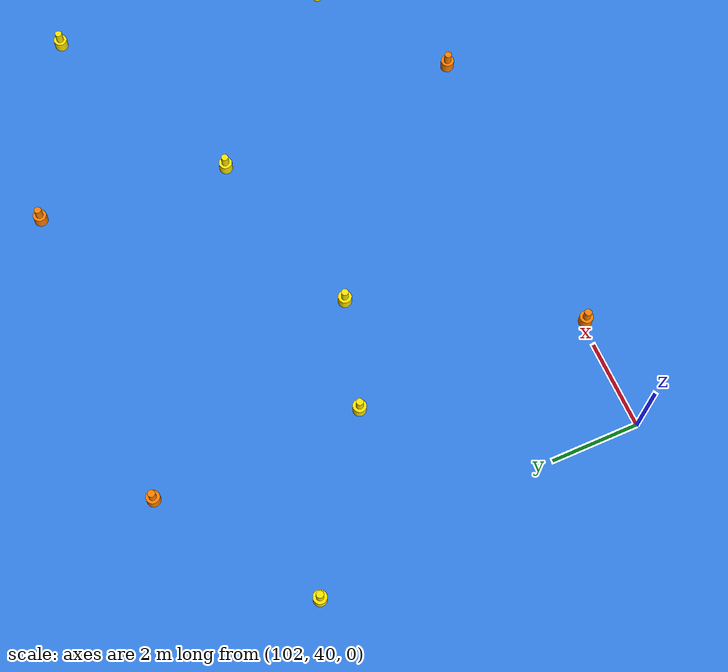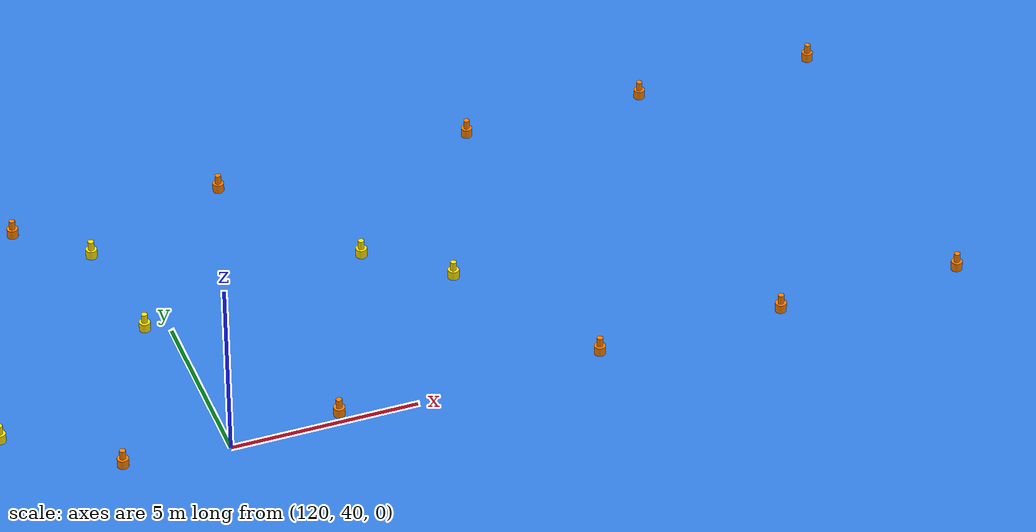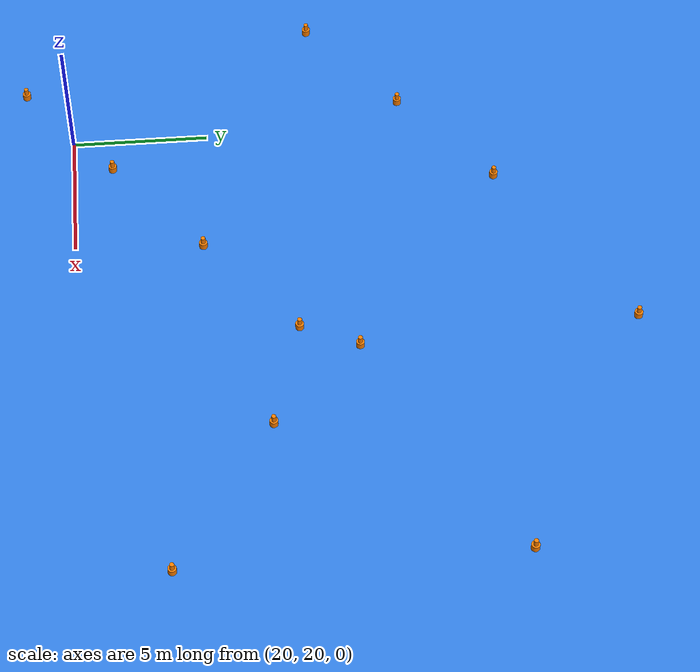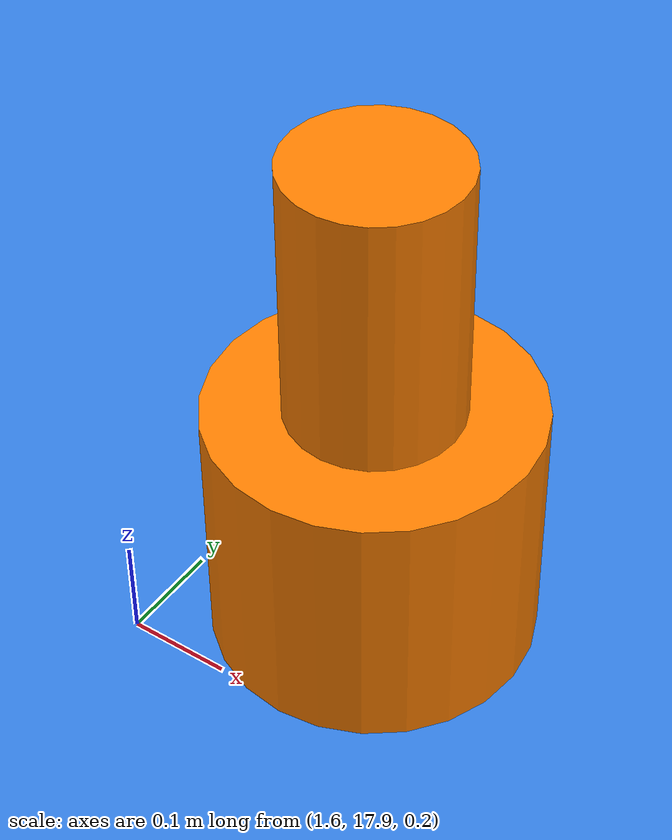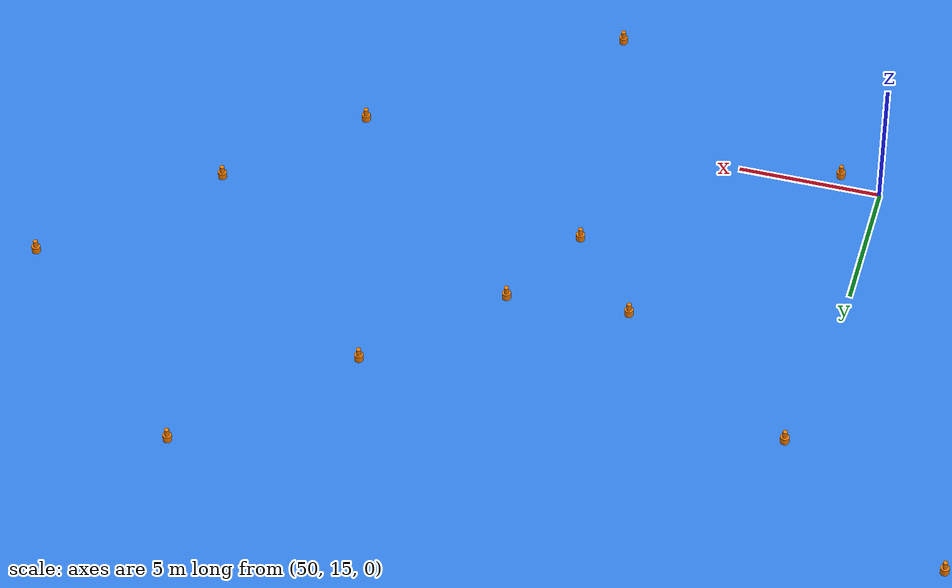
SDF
<?xml version="1.0" ?>
<sdf version="1.6">
  <world name="ida_sim">
    <!-- Güneş ışığı + ortam aydınlatması -->
    <include>
      <uri>model://sun</uri>
    </include>

    <light name="ambient_light" type="directional">
      <cast_shadows>true</cast_shadows>
      <pose>0 0 30 0 0 0</pose>
      <diffuse>0.9 0.9 0.9 1</diffuse>
      <specular>0.2 0.2 0.2 1</specular>
      <direction>-0.5 -0.5 -0.9</direction>
      <attenuation>
        <range>1000</range>
        <constant>0.9</constant>
        <linear>0.01</linear>
        <quadratic>0.001</quadratic>
      </attenuation>
    </light>

    <!-- Varsayılan fizik (yüzey yerçekimi, standart temas) -->
    <physics type="ode">
      <max_step_size>0.001</max_step_size>
      <real_time_factor>1</real_time_factor>
      <real_time_update_rate>1000</real_time_update_rate>
    </physics>

    <plugin name="gazebo_ros_state" filename="libgazebo_ros_state.so">
      <ros>
        <namespace>/gazebo</namespace>
      </ros>
      <update_rate>20</update_rate>
    </plugin>

    <!-- Su yüzeyi: z=0 düzleminde büyük mavi yarı saydam tabaka -->
    <model name="water_plane">
      <static>true</static>
      <link name="water_link">
        <collision name="water_collision">
          <pose>0 0 0 0 0 0</pose>
          <geometry>
            <plane>
              <normal>0 0 1</normal>
              <size>100 100</size>
            </plane>
          </geometry>
        </collision>
        <visual name="water_visual">
          <pose>0 0 0 0 0 0</pose>
          <geometry>
            <plane>
              <normal>0 0 1</normal>
              <size>100 100</size>
            </plane>
          </geometry>
          <material>
            <ambient>0.2 0.4 0.8 0.6</ambient>
            <diffuse>0.2 0.5 0.9 0.6</diffuse>
            <specular>0.1 0.1 0.1 1</specular>
          </material>
        </visual>
      </link>
    </model>

    <model name="ida_boat">
      <static>false</static>
      <pose>0 0 0.3 0 0 0</pose>
      <link name="boat_body">
        <pose>0 0 0.125 0 0 0</pose>
        <collision name="boat_body_collision">
          <geometry>
            <box>
              <size>1.4 0.9 0.25</size>
            </box>
          </geometry>
        </collision>
        <visual name="boat_body_visual">
          <geometry>
            <box>
              <size>1.4 0.9 0.25</size>
            </box>
          </geometry>
          <material>
            <ambient>1.0 0.55 0.15 1</ambient>
            <diffuse>1.0 0.6 0.2 1</diffuse>
          </material>
        </visual>
      </link>
      <link name="mast">
        <pose>0 0 0.25 0 0 0</pose>
        <visual name="mast_visual">
          <geometry>
            <cylinder>
              <radius>0.03</radius>
              <length>0.4</length>
            </cylinder>
          </geometry>
          <material>
            <ambient>0.9 0.9 0.9 1</ambient>
            <diffuse>1 1 1 1</diffuse>
          </material>
        </visual>
      </link>
      <!-- Kamera: tekne önüne (ENU +x) ve mast tepesine monte -->
      <link name="camera_link">
        <pose>0.5 0 0.5 0 0 0</pose>
        <inertial>
          <mass>0.05</mass>
          <inertia>
            <ixx>0.0001</ixx>
            <iyy>0.0001</iyy>
            <izz>0.0001</izz>
          </inertia>
        </inertial>
        <sensor name="camera_sensor" type="camera">
          <camera>
            <horizontal_fov>1.57</horizontal_fov>
            <image>
              <width>640</width>
              <height>480</height>
            </image>
            <clip>
              <near>0.1</near>
              <far>100</far>
            </clip>
          </camera>
          <update_rate>10</update_rate>
          <plugin name="ida_camera" filename="libgazebo_ros_camera.so">
            <ros>
              <namespace>/</namespace>
              <remapping>image_raw:=camera/image_raw</remapping>
            </ros>
            <camera_name>ida_camera</camera_name>
            <image_width>640</image_width>
            <image_height>480</image_height>
            <update_rate>10</update_rate>
            <horizontal_fov>1.57</horizontal_fov>
          </plugin>
        </sensor>
      </link>
      <!-- 2D Lidar (ray): mast üstü, 360 derece -->
      <link name="lidar_link">
        <pose>0.2 0 0.2 0 0 0</pose>
        <inertial>
          <mass>0.05</mass>
          <inertia>
            <ixx>0.0001</ixx>
            <iyy>0.0001</iyy>
            <izz>0.0001</izz>
          </inertia>
        </inertial>
        <sensor name="lidar_sensor" type="ray">
          <ray>
            <scan>
              <horizontal>
                <samples>360</samples>
                <resolution>1</resolution>
                <min_angle>-3.14159</min_angle>
                <max_angle>3.14159</max_angle>
              </horizontal>
            </scan>
            <range>
              <min>0.3</min>
              <max>18.0</max>
              <resolution>0.01</resolution>
            </range>
            <noise>
              <type>gaussian</type>
              <mean>0.0</mean>
              <stddev>0.01</stddev>
            </noise>
          </ray>
          <update_rate>10</update_rate>
          <plugin name="ida_lidar" filename="libgazebo_ros_ray_sensor.so">
            <ros>
              <namespace>/</namespace>
              <remapping>scan:=scan</remapping>
            </ros>
            <output_type>sensor_msgs/LaserScan</output_type>
            <update_rate>10</update_rate>
            <min_angle>-3.14159</min_angle>
            <max_angle>3.14159</max_angle>
            <range_min>0.3</range_min>
            <range_max>18.0</range_max>
          </plugin>
        </sensor>
      </link>
    </model>

<!-- ida_course_models.sdf — otomatik üretildi (tools/generate_course.py).
     Duba katmanı: world'e gömülür (ENU dönüşümü uygulanır);
     pozlar full_mission.yaml ile birebir. -->
  <model name="p1_o_l1" static="true">
    <pose>3.201 6.159 0.250 0 0 0</pose>
    <link name="p1_o_l1_link">
      <collision name="p1_o_l1_collision">
        <geometry>
          <cylinder>
            <radius>0.15</radius>
            <length>0.5</length>
          </cylinder>
        </geometry>
      </collision>
      <visual name="p1_o_l1_visual_bottom">
        <pose>0 0 0.125 0 0 0</pose>
        <geometry>
          <cylinder>
            <radius>0.15</radius>
            <length>0.25</length>
          </cylinder>
        </geometry>
        <material>
          <ambient>1.00 0.50 0.00 1.00</ambient>
          <diffuse>1.00 0.50 0.00 1.00</diffuse>
        </material>
      </visual>
      <visual name="p1_o_l1_visual_top">
        <pose>0 0 0.375 0 0 0</pose>
        <geometry>
          <cylinder>
            <radius>0.08</radius>
            <length>0.25</length>
          </cylinder>
        </geometry>
        <material>
          <ambient>1.00 0.50 0.00 1.00</ambient>
          <diffuse>1.00 0.50 0.00 1.00</diffuse>
        </material>
      </visual>
    </link>
  </model>
  <model name="p1_o_r1" static="true">
    <pose>-3.201 13.841 0.250 0 0 0</pose>
    <link name="p1_o_r1_link">
      <collision name="p1_o_r1_collision">
        <geometry>
          <cylinder>
            <radius>0.15</radius>
            <length>0.5</length>
          </cylinder>
        </geometry>
      </collision>
      <visual name="p1_o_r1_visual_bottom">
        <pose>0 0 0.125 0 0 0</pose>
        <geometry>
          <cylinder>
            <radius>0.15</radius>
            <length>0.25</length>
          </cylinder>
        </geometry>
        <material>
          <ambient>1.00 0.50 0.00 1.00</ambient>
          <diffuse>1.00 0.50 0.00 1.00</diffuse>
        </material>
      </visual>
      <visual name="p1_o_r1_visual_top">
        <pose>0 0 0.375 0 0 0</pose>
        <geometry>
          <cylinder>
            <radius>0.08</radius>
            <length>0.25</length>
          </cylinder>
        </geometry>
        <material>
          <ambient>1.00 0.50 0.00 1.00</ambient>
          <diffuse>1.00 0.50 0.00 1.00</diffuse>
        </material>
      </visual>
    </link>
  </model>
  <model name="p1_o_l2" static="true">
    <pose>8.200 10.325 0.250 0 0 0</pose>
    <link name="p1_o_l2_link">
      <collision name="p1_o_l2_collision">
        <geometry>
          <cylinder>
            <radius>0.15</radius>
            <length>0.5</length>
          </cylinder>
        </geometry>
      </collision>
      <visual name="p1_o_l2_visual_bottom">
        <pose>0 0 0.125 0 0 0</pose>
        <geometry>
          <cylinder>
            <radius>0.15</radius>
            <length>0.25</length>
          </cylinder>
        </geometry>
        <material>
          <ambient>1.00 0.50 0.00 1.00</ambient>
          <diffuse>1.00 0.50 0.00 1.00</diffuse>
        </material>
      </visual>
      <visual name="p1_o_l2_visual_top">
        <pose>0 0 0.375 0 0 0</pose>
        <geometry>
          <cylinder>
            <radius>0.08</radius>
            <length>0.25</length>
          </cylinder>
        </geometry>
        <material>
          <ambient>1.00 0.50 0.00 1.00</ambient>
          <diffuse>1.00 0.50 0.00 1.00</diffuse>
        </material>
      </visual>
    </link>
  </model>
  <model name="p1_o_r2" static="true">
    <pose>1.798 18.007 0.250 0 0 0</pose>
    <link name="p1_o_r2_link">
      <collision name="p1_o_r2_collision">
        <geometry>
          <cylinder>
            <radius>0.15</radius>
            <length>0.5</length>
          </cylinder>
        </geometry>
      </collision>
      <visual name="p1_o_r2_visual_bottom">
        <pose>0 0 0.125 0 0 0</pose>
        <geometry>
          <cylinder>
            <radius>0.15</radius>
            <length>0.25</length>
          </cylinder>
        </geometry>
        <material>
          <ambient>1.00 0.50 0.00 1.00</ambient>
          <diffuse>1.00 0.50 0.00 1.00</diffuse>
        </material>
      </visual>
      <visual name="p1_o_r2_visual_top">
        <pose>0 0 0.375 0 0 0</pose>
        <geometry>
          <cylinder>
            <radius>0.08</radius>
            <length>0.25</length>
          </cylinder>
        </geometry>
        <material>
          <ambient>1.00 0.50 0.00 1.00</ambient>
          <diffuse>1.00 0.50 0.00 1.00</diffuse>
        </material>
      </visual>
    </link>
  </model>
  <model name="p1_o_l3" static="true">
    <pose>13.041 14.359 0.250 0 0 0</pose>
    <link name="p1_o_l3_link">
      <collision name="p1_o_l3_collision">
        <geometry>
          <cylinder>
            <radius>0.15</radius>
            <length>0.5</length>
          </cylinder>
        </geometry>
      </collision>
      <visual name="p1_o_l3_visual_bottom">
        <pose>0 0 0.125 0 0 0</pose>
        <geometry>
          <cylinder>
            <radius>0.15</radius>
            <length>0.25</length>
          </cylinder>
        </geometry>
        <material>
          <ambient>1.00 0.50 0.00 1.00</ambient>
          <diffuse>1.00 0.50 0.00 1.00</diffuse>
        </material>
      </visual>
      <visual name="p1_o_l3_visual_top">
        <pose>0 0 0.375 0 0 0</pose>
        <geometry>
          <cylinder>
            <radius>0.08</radius>
            <length>0.25</length>
          </cylinder>
        </geometry>
        <material>
          <ambient>1.00 0.50 0.00 1.00</ambient>
          <diffuse>1.00 0.50 0.00 1.00</diffuse>
        </material>
      </visual>
    </link>
  </model>
  <model name="p1_o_r3" static="true">
    <pose>6.640 22.042 0.250 0 0 0</pose>
    <link name="p1_o_r3_link">
      <collision name="p1_o_r3_collision">
        <geometry>
          <cylinder>
            <radius>0.15</radius>
            <length>0.5</length>
          </cylinder>
        </geometry>
      </collision>
      <visual name="p1_o_r3_visual_bottom">
        <pose>0 0 0.125 0 0 0</pose>
        <geometry>
          <cylinder>
            <radius>0.15</radius>
            <length>0.25</length>
          </cylinder>
        </geometry>
        <material>
          <ambient>1.00 0.50 0.00 1.00</ambient>
          <diffuse>1.00 0.50 0.00 1.00</diffuse>
        </material>
      </visual>
      <visual name="p1_o_r3_visual_top">
        <pose>0 0 0.375 0 0 0</pose>
        <geometry>
          <cylinder>
            <radius>0.08</radius>
            <length>0.25</length>
          </cylinder>
        </geometry>
        <material>
          <ambient>1.00 0.50 0.00 1.00</ambient>
          <diffuse>1.00 0.50 0.00 1.00</diffuse>
        </material>
      </visual>
    </link>
  </model>
  <model name="p1_o_l4" static="true">
    <pose>17.703 18.244 0.250 0 0 0</pose>
    <link name="p1_o_l4_link">
      <collision name="p1_o_l4_collision">
        <geometry>
          <cylinder>
            <radius>0.15</radius>
            <length>0.5</length>
          </cylinder>
        </geometry>
      </collision>
      <visual name="p1_o_l4_visual_bottom">
        <pose>0 0 0.125 0 0 0</pose>
        <geometry>
          <cylinder>
            <radius>0.15</radius>
            <length>0.25</length>
          </cylinder>
        </geometry>
        <material>
          <ambient>1.00 0.50 0.00 1.00</ambient>
          <diffuse>1.00 0.50 0.00 1.00</diffuse>
        </material>
      </visual>
      <visual name="p1_o_l4_visual_top">
        <pose>0 0 0.375 0 0 0</pose>
        <geometry>
          <cylinder>
            <radius>0.08</radius>
            <length>0.25</length>
          </cylinder>
        </geometry>
        <material>
          <ambient>1.00 0.50 0.00 1.00</ambient>
          <diffuse>1.00 0.50 0.00 1.00</diffuse>
        </material>
      </visual>
    </link>
  </model>
  <model name="p1_o_r4" static="true">
    <pose>11.301 25.926 0.250 0 0 0</pose>
    <link name="p1_o_r4_link">
      <collision name="p1_o_r4_collision">
        <geometry>
          <cylinder>
            <radius>0.15</radius>
            <length>0.5</length>
          </cylinder>
        </geometry>
      </collision>
      <visual name="p1_o_r4_visual_bottom">
        <pose>0 0 0.125 0 0 0</pose>
        <geometry>
          <cylinder>
            <radius>0.15</radius>
            <length>0.25</length>
          </cylinder>
        </geometry>
        <material>
          <ambient>1.00 0.50 0.00 1.00</ambient>
          <diffuse>1.00 0.50 0.00 1.00</diffuse>
        </material>
      </visual>
      <visual name="p1_o_r4_visual_top">
        <pose>0 0 0.375 0 0 0</pose>
        <geometry>
          <cylinder>
            <radius>0.08</radius>
            <length>0.25</length>
          </cylinder>
        </geometry>
        <material>
          <ambient>1.00 0.50 0.00 1.00</ambient>
          <diffuse>1.00 0.50 0.00 1.00</diffuse>
        </material>
      </visual>
    </link>
  </model>
  <model name="p1_o_l5" static="true">
    <pose>21.558 21.456 0.250 0 0 0</pose>
    <link name="p1_o_l5_link">
      <collision name="p1_o_l5_collision">
        <geometry>
          <cylinder>
            <radius>0.15</radius>
            <length>0.5</length>
          </cylinder>
        </geometry>
      </collision>
      <visual name="p1_o_l5_visual_bottom">
        <pose>0 0 0.125 0 0 0</pose>
        <geometry>
          <cylinder>
            <radius>0.15</radius>
            <length>0.25</length>
          </cylinder>
        </geometry>
        <material>
          <ambient>1.00 0.50 0.00 1.00</ambient>
          <diffuse>1.00 0.50 0.00 1.00</diffuse>
        </material>
      </visual>
      <visual name="p1_o_l5_visual_top">
        <pose>0 0 0.375 0 0 0</pose>
        <geometry>
          <cylinder>
            <radius>0.08</radius>
            <length>0.25</length>
          </cylinder>
        </geometry>
        <material>
          <ambient>1.00 0.50 0.00 1.00</ambient>
          <diffuse>1.00 0.50 0.00 1.00</diffuse>
        </material>
      </visual>
    </link>
  </model>
  <model name="p1_o_r5" static="true">
    <pose>15.156 29.138 0.250 0 0 0</pose>
    <link name="p1_o_r5_link">
      <collision name="p1_o_r5_collision">
        <geometry>
          <cylinder>
            <radius>0.15</radius>
            <length>0.5</length>
          </cylinder>
        </geometry>
      </collision>
      <visual name="p1_o_r5_visual_bottom">
        <pose>0 0 0.125 0 0 0</pose>
        <geometry>
          <cylinder>
            <radius>0.15</radius>
            <length>0.25</length>
          </cylinder>
        </geometry>
        <material>
          <ambient>1.00 0.50 0.00 1.00</ambient>
          <diffuse>1.00 0.50 0.00 1.00</diffuse>
        </material>
      </visual>
      <visual name="p1_o_r5_visual_top">
        <pose>0 0 0.375 0 0 0</pose>
        <geometry>
          <cylinder>
            <radius>0.08</radius>
            <length>0.25</length>
          </cylinder>
        </geometry>
        <material>
          <ambient>1.00 0.50 0.00 1.00</ambient>
          <diffuse>1.00 0.50 0.00 1.00</diffuse>
        </material>
      </visual>
    </link>
  </model>
  <model name="p1_o_l6" static="true">
    <pose>25.426 24.679 0.250 0 0 0</pose>
    <link name="p1_o_l6_link">
      <collision name="p1_o_l6_collision">
        <geometry>
          <cylinder>
            <radius>0.15</radius>
            <length>0.5</length>
          </cylinder>
        </geometry>
      </collision>
      <visual name="p1_o_l6_visual_bottom">
        <pose>0 0 0.125 0 0 0</pose>
        <geometry>
          <cylinder>
            <radius>0.15</radius>
            <length>0.25</length>
          </cylinder>
        </geometry>
        <material>
          <ambient>1.00 0.50 0.00 1.00</ambient>
          <diffuse>1.00 0.50 0.00 1.00</diffuse>
        </material>
      </visual>
      <visual name="p1_o_l6_visual_top">
        <pose>0 0 0.375 0 0 0</pose>
        <geometry>
          <cylinder>
            <radius>0.08</radius>
            <length>0.25</length>
          </cylinder>
        </geometry>
        <material>
          <ambient>1.00 0.50 0.00 1.00</ambient>
          <diffuse>1.00 0.50 0.00 1.00</diffuse>
        </material>
      </visual>
    </link>
  </model>
  <model name="p1_o_r6" static="true">
    <pose>19.024 32.362 0.250 0 0 0</pose>
    <link name="p1_o_r6_link">
      <collision name="p1_o_r6_collision">
        <geometry>
          <cylinder>
            <radius>0.15</radius>
            <length>0.5</length>
          </cylinder>
        </geometry>
      </collision>
      <visual name="p1_o_r6_visual_bottom">
        <pose>0 0 0.125 0 0 0</pose>
        <geometry>
          <cylinder>
            <radius>0.15</radius>
            <length>0.25</length>
          </cylinder>
        </geometry>
        <material>
          <ambient>1.00 0.50 0.00 1.00</ambient>
          <diffuse>1.00 0.50 0.00 1.00</diffuse>
        </material>
      </visual>
      <visual name="p1_o_r6_visual_top">
        <pose>0 0 0.375 0 0 0</pose>
        <geometry>
          <cylinder>
            <radius>0.08</radius>
            <length>0.25</length>
          </cylinder>
        </geometry>
        <material>
          <ambient>1.00 0.50 0.00 1.00</ambient>
          <diffuse>1.00 0.50 0.00 1.00</diffuse>
        </material>
      </visual>
    </link>
  </model>
  <model name="p1_o_l7" static="true">
    <pose>29.323 27.927 0.250 0 0 0</pose>
    <link name="p1_o_l7_link">
      <collision name="p1_o_l7_collision">
        <geometry>
          <cylinder>
            <radius>0.15</radius>
            <length>0.5</length>
          </cylinder>
        </geometry>
      </collision>
      <visual name="p1_o_l7_visual_bottom">
        <pose>0 0 0.125 0 0 0</pose>
        <geometry>
          <cylinder>
            <radius>0.15</radius>
            <length>0.25</length>
          </cylinder>
        </geometry>
        <material>
          <ambient>1.00 0.50 0.00 1.00</ambient>
          <diffuse>1.00 0.50 0.00 1.00</diffuse>
        </material>
      </visual>
      <visual name="p1_o_l7_visual_top">
        <pose>0 0 0.375 0 0 0</pose>
        <geometry>
          <cylinder>
            <radius>0.08</radius>
            <length>0.25</length>
          </cylinder>
        </geometry>
        <material>
          <ambient>1.00 0.50 0.00 1.00</ambient>
          <diffuse>1.00 0.50 0.00 1.00</diffuse>
        </material>
      </visual>
    </link>
  </model>
  <model name="p1_o_r7" static="true">
    <pose>22.921 35.609 0.250 0 0 0</pose>
    <link name="p1_o_r7_link">
      <collision name="p1_o_r7_collision">
        <geometry>
          <cylinder>
            <radius>0.15</radius>
            <length>0.5</length>
          </cylinder>
        </geometry>
      </collision>
      <visual name="p1_o_r7_visual_bottom">
        <pose>0 0 0.125 0 0 0</pose>
        <geometry>
          <cylinder>
            <radius>0.15</radius>
            <length>0.25</length>
          </cylinder>
        </geometry>
        <material>
          <ambient>1.00 0.50 0.00 1.00</ambient>
          <diffuse>1.00 0.50 0.00 1.00</diffuse>
        </material>
      </visual>
      <visual name="p1_o_r7_visual_top">
        <pose>0 0 0.375 0 0 0</pose>
        <geometry>
          <cylinder>
            <radius>0.08</radius>
            <length>0.25</length>
          </cylinder>
        </geometry>
        <material>
          <ambient>1.00 0.50 0.00 1.00</ambient>
          <diffuse>1.00 0.50 0.00 1.00</diffuse>
        </material>
      </visual>
    </link>
  </model>
  <model name="p1_o_l8" static="true">
    <pose>30.267 30.007 0.250 0 0 0</pose>
    <link name="p1_o_l8_link">
      <collision name="p1_o_l8_collision">
        <geometry>
          <cylinder>
            <radius>0.15</radius>
            <length>0.5</length>
          </cylinder>
        </geometry>
      </collision>
      <visual name="p1_o_l8_visual_bottom">
        <pose>0 0 0.125 0 0 0</pose>
        <geometry>
          <cylinder>
            <radius>0.15</radius>
            <length>0.25</length>
          </cylinder>
        </geometry>
        <material>
          <ambient>1.00 0.50 0.00 1.00</ambient>
          <diffuse>1.00 0.50 0.00 1.00</diffuse>
        </material>
      </visual>
      <visual name="p1_o_l8_visual_top">
        <pose>0 0 0.375 0 0 0</pose>
        <geometry>
          <cylinder>
            <radius>0.08</radius>
            <length>0.25</length>
          </cylinder>
        </geometry>
        <material>
          <ambient>1.00 0.50 0.00 1.00</ambient>
          <diffuse>1.00 0.50 0.00 1.00</diffuse>
        </material>
      </visual>
    </link>
  </model>
  <model name="p1_o_r8" static="true">
    <pose>29.733 39.993 0.250 0 0 0</pose>
    <link name="p1_o_r8_link">
      <collision name="p1_o_r8_collision">
        <geometry>
          <cylinder>
            <radius>0.15</radius>
            <length>0.5</length>
          </cylinder>
        </geometry>
      </collision>
      <visual name="p1_o_r8_visual_bottom">
        <pose>0 0 0.125 0 0 0</pose>
        <geometry>
          <cylinder>
            <radius>0.15</radius>
            <length>0.25</length>
          </cylinder>
        </geometry>
        <material>
          <ambient>1.00 0.50 0.00 1.00</ambient>
          <diffuse>1.00 0.50 0.00 1.00</diffuse>
        </material>
      </visual>
      <visual name="p1_o_r8_visual_top">
        <pose>0 0 0.375 0 0 0</pose>
        <geometry>
          <cylinder>
            <radius>0.08</radius>
            <length>0.25</length>
          </cylinder>
        </geometry>
        <material>
          <ambient>1.00 0.50 0.00 1.00</ambient>
          <diffuse>1.00 0.50 0.00 1.00</diffuse>
        </material>
      </visual>
    </link>
  </model>
  <model name="p1_o_l9" static="true">
    <pose>33.342 26.763 0.250 0 0 0</pose>
    <link name="p1_o_l9_link">
      <collision name="p1_o_l9_collision">
        <geometry>
          <cylinder>
            <radius>0.15</radius>
            <length>0.5</length>
          </cylinder>
        </geometry>
      </collision>
      <visual name="p1_o_l9_visual_bottom">
        <pose>0 0 0.125 0 0 0</pose>
        <geometry>
          <cylinder>
            <radius>0.15</radius>
            <length>0.25</length>
          </cylinder>
        </geometry>
        <material>
          <ambient>1.00 0.50 0.00 1.00</ambient>
          <diffuse>1.00 0.50 0.00 1.00</diffuse>
        </material>
      </visual>
      <visual name="p1_o_l9_visual_top">
        <pose>0 0 0.375 0 0 0</pose>
        <geometry>
          <cylinder>
            <radius>0.08</radius>
            <length>0.25</length>
          </cylinder>
        </geometry>
        <material>
          <ambient>1.00 0.50 0.00 1.00</ambient>
          <diffuse>1.00 0.50 0.00 1.00</diffuse>
        </material>
      </visual>
    </link>
  </model>
  <model name="p1_o_r9" static="true">
    <pose>38.889 35.083 0.250 0 0 0</pose>
    <link name="p1_o_r9_link">
      <collision name="p1_o_r9_collision">
        <geometry>
          <cylinder>
            <radius>0.15</radius>
            <length>0.5</length>
          </cylinder>
        </geometry>
      </collision>
      <visual name="p1_o_r9_visual_bottom">
        <pose>0 0 0.125 0 0 0</pose>
        <geometry>
          <cylinder>
            <radius>0.15</radius>
            <length>0.25</length>
          </cylinder>
        </geometry>
        <material>
          <ambient>1.00 0.50 0.00 1.00</ambient>
          <diffuse>1.00 0.50 0.00 1.00</diffuse>
        </material>
      </visual>
      <visual name="p1_o_r9_visual_top">
        <pose>0 0 0.375 0 0 0</pose>
        <geometry>
          <cylinder>
            <radius>0.08</radius>
            <length>0.25</length>
          </cylinder>
        </geometry>
        <material>
          <ambient>1.00 0.50 0.00 1.00</ambient>
          <diffuse>1.00 0.50 0.00 1.00</diffuse>
        </material>
      </visual>
    </link>
  </model>
  <model name="p1_o_l10" static="true">
    <pose>38.870 23.078 0.250 0 0 0</pose>
    <link name="p1_o_l10_link">
      <collision name="p1_o_l10_collision">
        <geometry>
          <cylinder>
            <radius>0.15</radius>
            <length>0.5</length>
          </cylinder>
        </geometry>
      </collision>
      <visual name="p1_o_l10_visual_bottom">
        <pose>0 0 0.125 0 0 0</pose>
        <geometry>
          <cylinder>
            <radius>0.15</radius>
            <length>0.25</length>
          </cylinder>
        </geometry>
        <material>
          <ambient>1.00 0.50 0.00 1.00</ambient>
          <diffuse>1.00 0.50 0.00 1.00</diffuse>
        </material>
      </visual>
      <visual name="p1_o_l10_visual_top">
        <pose>0 0 0.375 0 0 0</pose>
        <geometry>
          <cylinder>
            <radius>0.08</radius>
            <length>0.25</length>
          </cylinder>
        </geometry>
        <material>
          <ambient>1.00 0.50 0.00 1.00</ambient>
          <diffuse>1.00 0.50 0.00 1.00</diffuse>
        </material>
      </visual>
    </link>
  </model>
  <model name="p1_o_r10" static="true">
    <pose>44.417 31.398 0.250 0 0 0</pose>
    <link name="p1_o_r10_link">
      <collision name="p1_o_r10_collision">
        <geometry>
          <cylinder>
            <radius>0.15</radius>
            <length>0.5</length>
          </cylinder>
        </geometry>
      </collision>
      <visual name="p1_o_r10_visual_bottom">
        <pose>0 0 0.125 0 0 0</pose>
        <geometry>
          <cylinder>
            <radius>0.15</radius>
            <length>0.25</length>
          </cylinder>
        </geometry>
        <material>
          <ambient>1.00 0.50 0.00 1.00</ambient>
          <diffuse>1.00 0.50 0.00 1.00</diffuse>
        </material>
      </visual>
      <visual name="p1_o_r10_visual_top">
        <pose>0 0 0.375 0 0 0</pose>
        <geometry>
          <cylinder>
            <radius>0.08</radius>
            <length>0.25</length>
          </cylinder>
        </geometry>
        <material>
          <ambient>1.00 0.50 0.00 1.00</ambient>
          <diffuse>1.00 0.50 0.00 1.00</diffuse>
        </material>
      </visual>
    </link>
  </model>
  <model name="p1_o_l11" static="true">
    <pose>45.092 18.930 0.250 0 0 0</pose>
    <link name="p1_o_l11_link">
      <collision name="p1_o_l11_collision">
        <geometry>
          <cylinder>
            <radius>0.15</radius>
            <length>0.5</length>
          </cylinder>
        </geometry>
      </collision>
      <visual name="p1_o_l11_visual_bottom">
        <pose>0 0 0.125 0 0 0</pose>
        <geometry>
          <cylinder>
            <radius>0.15</radius>
            <length>0.25</length>
          </cylinder>
        </geometry>
        <material>
          <ambient>1.00 0.50 0.00 1.00</ambient>
          <diffuse>1.00 0.50 0.00 1.00</diffuse>
        </material>
      </visual>
      <visual name="p1_o_l11_visual_top">
        <pose>0 0 0.375 0 0 0</pose>
        <geometry>
          <cylinder>
            <radius>0.08</radius>
            <length>0.25</length>
          </cylinder>
        </geometry>
        <material>
          <ambient>1.00 0.50 0.00 1.00</ambient>
          <diffuse>1.00 0.50 0.00 1.00</diffuse>
        </material>
      </visual>
    </link>
  </model>
  <model name="p1_o_r11" static="true">
    <pose>50.639 27.250 0.250 0 0 0</pose>
    <link name="p1_o_r11_link">
      <collision name="p1_o_r11_collision">
        <geometry>
          <cylinder>
            <radius>0.15</radius>
            <length>0.5</length>
          </cylinder>
        </geometry>
      </collision>
      <visual name="p1_o_r11_visual_bottom">
        <pose>0 0 0.125 0 0 0</pose>
        <geometry>
          <cylinder>
            <radius>0.15</radius>
            <length>0.25</length>
          </cylinder>
        </geometry>
        <material>
          <ambient>1.00 0.50 0.00 1.00</ambient>
          <diffuse>1.00 0.50 0.00 1.00</diffuse>
        </material>
      </visual>
      <visual name="p1_o_r11_visual_top">
        <pose>0 0 0.375 0 0 0</pose>
        <geometry>
          <cylinder>
            <radius>0.08</radius>
            <length>0.25</length>
          </cylinder>
        </geometry>
        <material>
          <ambient>1.00 0.50 0.00 1.00</ambient>
          <diffuse>1.00 0.50 0.00 1.00</diffuse>
        </material>
      </visual>
    </link>
  </model>
  <model name="p1_o_l12" static="true">
    <pose>51.475 14.674 0.250 0 0 0</pose>
    <link name="p1_o_l12_link">
      <collision name="p1_o_l12_collision">
        <geometry>
          <cylinder>
            <radius>0.15</radius>
            <length>0.5</length>
          </cylinder>
        </geometry>
      </collision>
      <visual name="p1_o_l12_visual_bottom">
        <pose>0 0 0.125 0 0 0</pose>
        <geometry>
          <cylinder>
            <radius>0.15</radius>
            <length>0.25</length>
          </cylinder>
        </geometry>
        <material>
          <ambient>1.00 0.50 0.00 1.00</ambient>
          <diffuse>1.00 0.50 0.00 1.00</diffuse>
        </material>
      </visual>
      <visual name="p1_o_l12_visual_top">
        <pose>0 0 0.375 0 0 0</pose>
        <geometry>
          <cylinder>
            <radius>0.08</radius>
            <length>0.25</length>
          </cylinder>
        </geometry>
        <material>
          <ambient>1.00 0.50 0.00 1.00</ambient>
          <diffuse>1.00 0.50 0.00 1.00</diffuse>
        </material>
      </visual>
    </link>
  </model>
  <model name="p1_o_r12" static="true">
    <pose>57.022 22.995 0.250 0 0 0</pose>
    <link name="p1_o_r12_link">
      <collision name="p1_o_r12_collision">
        <geometry>
          <cylinder>
            <radius>0.15</radius>
            <length>0.5</length>
          </cylinder>
        </geometry>
      </collision>
      <visual name="p1_o_r12_visual_bottom">
        <pose>0 0 0.125 0 0 0</pose>
        <geometry>
          <cylinder>
            <radius>0.15</radius>
            <length>0.25</length>
          </cylinder>
        </geometry>
        <material>
          <ambient>1.00 0.50 0.00 1.00</ambient>
          <diffuse>1.00 0.50 0.00 1.00</diffuse>
        </material>
      </visual>
      <visual name="p1_o_r12_visual_top">
        <pose>0 0 0.375 0 0 0</pose>
        <geometry>
          <cylinder>
            <radius>0.08</radius>
            <length>0.25</length>
          </cylinder>
        </geometry>
        <material>
          <ambient>1.00 0.50 0.00 1.00</ambient>
          <diffuse>1.00 0.50 0.00 1.00</diffuse>
        </material>
      </visual>
    </link>
  </model>
  <model name="p1_o_l13" static="true">
    <pose>60.493 10.024 0.250 0 0 0</pose>
    <link name="p1_o_l13_link">
      <collision name="p1_o_l13_collision">
        <geometry>
          <cylinder>
            <radius>0.15</radius>
            <length>0.5</length>
          </cylinder>
        </geometry>
      </collision>
      <visual name="p1_o_l13_visual_bottom">
        <pose>0 0 0.125 0 0 0</pose>
        <geometry>
          <cylinder>
            <radius>0.15</radius>
            <length>0.25</length>
          </cylinder>
        </geometry>
        <material>
          <ambient>1.00 0.50 0.00 1.00</ambient>
          <diffuse>1.00 0.50 0.00 1.00</diffuse>
        </material>
      </visual>
      <visual name="p1_o_l13_visual_top">
        <pose>0 0 0.375 0 0 0</pose>
        <geometry>
          <cylinder>
            <radius>0.08</radius>
            <length>0.25</length>
          </cylinder>
        </geometry>
        <material>
          <ambient>1.00 0.50 0.00 1.00</ambient>
          <diffuse>1.00 0.50 0.00 1.00</diffuse>
        </material>
      </visual>
    </link>
  </model>
  <model name="p1_o_r13" static="true">
    <pose>59.507 19.976 0.250 0 0 0</pose>
    <link name="p1_o_r13_link">
      <collision name="p1_o_r13_collision">
        <geometry>
          <cylinder>
            <radius>0.15</radius>
            <length>0.5</length>
          </cylinder>
        </geometry>
      </collision>
      <visual name="p1_o_r13_visual_bottom">
        <pose>0 0 0.125 0 0 0</pose>
        <geometry>
          <cylinder>
            <radius>0.15</radius>
            <length>0.25</length>
          </cylinder>
        </geometry>
        <material>
          <ambient>1.00 0.50 0.00 1.00</ambient>
          <diffuse>1.00 0.50 0.00 1.00</diffuse>
        </material>
      </visual>
      <visual name="p1_o_r13_visual_top">
        <pose>0 0 0.375 0 0 0</pose>
        <geometry>
          <cylinder>
            <radius>0.08</radius>
            <length>0.25</length>
          </cylinder>
        </geometry>
        <material>
          <ambient>1.00 0.50 0.00 1.00</ambient>
          <diffuse>1.00 0.50 0.00 1.00</diffuse>
        </material>
      </visual>
    </link>
  </model>
  <model name="p1_o_l14" static="true">
    <pose>68.315 16.244 0.250 0 0 0</pose>
    <link name="p1_o_l14_link">
      <collision name="p1_o_l14_collision">
        <geometry>
          <cylinder>
            <radius>0.15</radius>
            <length>0.5</length>
          </cylinder>
        </geometry>
      </collision>
      <visual name="p1_o_l14_visual_bottom">
        <pose>0 0 0.125 0 0 0</pose>
        <geometry>
          <cylinder>
            <radius>0.15</radius>
            <length>0.25</length>
          </cylinder>
        </geometry>
        <material>
          <ambient>1.00 0.50 0.00 1.00</ambient>
          <diffuse>1.00 0.50 0.00 1.00</diffuse>
        </material>
      </visual>
      <visual name="p1_o_l14_visual_top">
        <pose>0 0 0.375 0 0 0</pose>
        <geometry>
          <cylinder>
            <radius>0.08</radius>
            <length>0.25</length>
          </cylinder>
        </geometry>
        <material>
          <ambient>1.00 0.50 0.00 1.00</ambient>
          <diffuse>1.00 0.50 0.00 1.00</diffuse>
        </material>
      </visual>
    </link>
  </model>
  <model name="p1_o_r14" static="true">
    <pose>61.244 23.315 0.250 0 0 0</pose>
    <link name="p1_o_r14_link">
      <collision name="p1_o_r14_collision">
        <geometry>
          <cylinder>
            <radius>0.15</radius>
            <length>0.5</length>
          </cylinder>
        </geometry>
      </collision>
      <visual name="p1_o_r14_visual_bottom">
        <pose>0 0 0.125 0 0 0</pose>
        <geometry>
          <cylinder>
            <radius>0.15</radius>
            <length>0.25</length>
          </cylinder>
        </geometry>
        <material>
          <ambient>1.00 0.50 0.00 1.00</ambient>
          <diffuse>1.00 0.50 0.00 1.00</diffuse>
        </material>
      </visual>
      <visual name="p1_o_r14_visual_top">
        <pose>0 0 0.375 0 0 0</pose>
        <geometry>
          <cylinder>
            <radius>0.08</radius>
            <length>0.25</length>
          </cylinder>
        </geometry>
        <material>
          <ambient>1.00 0.50 0.00 1.00</ambient>
          <diffuse>1.00 0.50 0.00 1.00</diffuse>
        </material>
      </visual>
    </link>
  </model>
  <model name="p1_o_l15" static="true">
    <pose>72.360 20.289 0.250 0 0 0</pose>
    <link name="p1_o_l15_link">
      <collision name="p1_o_l15_collision">
        <geometry>
          <cylinder>
            <radius>0.15</radius>
            <length>0.5</length>
          </cylinder>
        </geometry>
      </collision>
      <visual name="p1_o_l15_visual_bottom">
        <pose>0 0 0.125 0 0 0</pose>
        <geometry>
          <cylinder>
            <radius>0.15</radius>
            <length>0.25</length>
          </cylinder>
        </geometry>
        <material>
          <ambient>1.00 0.50 0.00 1.00</ambient>
          <diffuse>1.00 0.50 0.00 1.00</diffuse>
        </material>
      </visual>
      <visual name="p1_o_l15_visual_top">
        <pose>0 0 0.375 0 0 0</pose>
        <geometry>
          <cylinder>
            <radius>0.08</radius>
            <length>0.25</length>
          </cylinder>
        </geometry>
        <material>
          <ambient>1.00 0.50 0.00 1.00</ambient>
          <diffuse>1.00 0.50 0.00 1.00</diffuse>
        </material>
      </visual>
    </link>
  </model>
  <model name="p1_o_r15" static="true">
    <pose>65.289 27.360 0.250 0 0 0</pose>
    <link name="p1_o_r15_link">
      <collision name="p1_o_r15_collision">
        <geometry>
          <cylinder>
            <radius>0.15</radius>
            <length>0.5</length>
          </cylinder>
        </geometry>
      </collision>
      <visual name="p1_o_r15_visual_bottom">
        <pose>0 0 0.125 0 0 0</pose>
        <geometry>
          <cylinder>
            <radius>0.15</radius>
            <length>0.25</length>
          </cylinder>
        </geometry>
        <material>
          <ambient>1.00 0.50 0.00 1.00</ambient>
          <diffuse>1.00 0.50 0.00 1.00</diffuse>
        </material>
      </visual>
      <visual name="p1_o_r15_visual_top">
        <pose>0 0 0.375 0 0 0</pose>
        <geometry>
          <cylinder>
            <radius>0.08</radius>
            <length>0.25</length>
          </cylinder>
        </geometry>
        <material>
          <ambient>1.00 0.50 0.00 1.00</ambient>
          <diffuse>1.00 0.50 0.00 1.00</diffuse>
        </material>
      </visual>
    </link>
  </model>
  <model name="p1_o_l16" static="true">
    <pose>77.457 25.386 0.250 0 0 0</pose>
    <link name="p1_o_l16_link">
      <collision name="p1_o_l16_collision">
        <geometry>
          <cylinder>
            <radius>0.15</radius>
            <length>0.5</length>
          </cylinder>
        </geometry>
      </collision>
      <visual name="p1_o_l16_visual_bottom">
        <pose>0 0 0.125 0 0 0</pose>
        <geometry>
          <cylinder>
            <radius>0.15</radius>
            <length>0.25</length>
          </cylinder>
        </geometry>
        <material>
          <ambient>1.00 0.50 0.00 1.00</ambient>
          <diffuse>1.00 0.50 0.00 1.00</diffuse>
        </material>
      </visual>
      <visual name="p1_o_l16_visual_top">
        <pose>0 0 0.375 0 0 0</pose>
        <geometry>
          <cylinder>
            <radius>0.08</radius>
            <length>0.25</length>
          </cylinder>
        </geometry>
        <material>
          <ambient>1.00 0.50 0.00 1.00</ambient>
          <diffuse>1.00 0.50 0.00 1.00</diffuse>
        </material>
      </visual>
    </link>
  </model>
  <model name="p1_o_r16" static="true">
    <pose>70.386 32.457 0.250 0 0 0</pose>
    <link name="p1_o_r16_link">
      <collision name="p1_o_r16_collision">
        <geometry>
          <cylinder>
            <radius>0.15</radius>
            <length>0.5</length>
          </cylinder>
        </geometry>
      </collision>
      <visual name="p1_o_r16_visual_bottom">
        <pose>0 0 0.125 0 0 0</pose>
        <geometry>
          <cylinder>
            <radius>0.15</radius>
            <length>0.25</length>
          </cylinder>
        </geometry>
        <material>
          <ambient>1.00 0.50 0.00 1.00</ambient>
          <diffuse>1.00 0.50 0.00 1.00</diffuse>
        </material>
      </visual>
      <visual name="p1_o_r16_visual_top">
        <pose>0 0 0.375 0 0 0</pose>
        <geometry>
          <cylinder>
            <radius>0.08</radius>
            <length>0.25</length>
          </cylinder>
        </geometry>
        <material>
          <ambient>1.00 0.50 0.00 1.00</ambient>
          <diffuse>1.00 0.50 0.00 1.00</diffuse>
        </material>
      </visual>
    </link>
  </model>
  <model name="p1_o_l17" static="true">
    <pose>82.321 30.249 0.250 0 0 0</pose>
    <link name="p1_o_l17_link">
      <collision name="p1_o_l17_collision">
        <geometry>
          <cylinder>
            <radius>0.15</radius>
            <length>0.5</length>
          </cylinder>
        </geometry>
      </collision>
      <visual name="p1_o_l17_visual_bottom">
        <pose>0 0 0.125 0 0 0</pose>
        <geometry>
          <cylinder>
            <radius>0.15</radius>
            <length>0.25</length>
          </cylinder>
        </geometry>
        <material>
          <ambient>1.00 0.50 0.00 1.00</ambient>
          <diffuse>1.00 0.50 0.00 1.00</diffuse>
        </material>
      </visual>
      <visual name="p1_o_l17_visual_top">
        <pose>0 0 0.375 0 0 0</pose>
        <geometry>
          <cylinder>
            <radius>0.08</radius>
            <length>0.25</length>
          </cylinder>
        </geometry>
        <material>
          <ambient>1.00 0.50 0.00 1.00</ambient>
          <diffuse>1.00 0.50 0.00 1.00</diffuse>
        </material>
      </visual>
    </link>
  </model>
  <model name="p1_o_r17" static="true">
    <pose>75.249 37.321 0.250 0 0 0</pose>
    <link name="p1_o_r17_link">
      <collision name="p1_o_r17_collision">
        <geometry>
          <cylinder>
            <radius>0.15</radius>
            <length>0.5</length>
          </cylinder>
        </geometry>
      </collision>
      <visual name="p1_o_r17_visual_bottom">
        <pose>0 0 0.125 0 0 0</pose>
        <geometry>
          <cylinder>
            <radius>0.15</radius>
            <length>0.25</length>
          </cylinder>
        </geometry>
        <material>
          <ambient>1.00 0.50 0.00 1.00</ambient>
          <diffuse>1.00 0.50 0.00 1.00</diffuse>
        </material>
      </visual>
      <visual name="p1_o_r17_visual_top">
        <pose>0 0 0.375 0 0 0</pose>
        <geometry>
          <cylinder>
            <radius>0.08</radius>
            <length>0.25</length>
          </cylinder>
        </geometry>
        <material>
          <ambient>1.00 0.50 0.00 1.00</ambient>
          <diffuse>1.00 0.50 0.00 1.00</diffuse>
        </material>
      </visual>
    </link>
  </model>
  <model name="p1_o_l18" static="true">
    <pose>87.959 35.888 0.250 0 0 0</pose>
    <link name="p1_o_l18_link">
      <collision name="p1_o_l18_collision">
        <geometry>
          <cylinder>
            <radius>0.15</radius>
            <length>0.5</length>
          </cylinder>
        </geometry>
      </collision>
      <visual name="p1_o_l18_visual_bottom">
        <pose>0 0 0.125 0 0 0</pose>
        <geometry>
          <cylinder>
            <radius>0.15</radius>
            <length>0.25</length>
          </cylinder>
        </geometry>
        <material>
          <ambient>1.00 0.50 0.00 1.00</ambient>
          <diffuse>1.00 0.50 0.00 1.00</diffuse>
        </material>
      </visual>
      <visual name="p1_o_l18_visual_top">
        <pose>0 0 0.375 0 0 0</pose>
        <geometry>
          <cylinder>
            <radius>0.08</radius>
            <length>0.25</length>
          </cylinder>
        </geometry>
        <material>
          <ambient>1.00 0.50 0.00 1.00</ambient>
          <diffuse>1.00 0.50 0.00 1.00</diffuse>
        </material>
      </visual>
    </link>
  </model>
  <model name="p1_o_r18" static="true">
    <pose>80.888 42.959 0.250 0 0 0</pose>
    <link name="p1_o_r18_link">
      <collision name="p1_o_r18_collision">
        <geometry>
          <cylinder>
            <radius>0.15</radius>
            <length>0.5</length>
          </cylinder>
        </geometry>
      </collision>
      <visual name="p1_o_r18_visual_bottom">
        <pose>0 0 0.125 0 0 0</pose>
        <geometry>
          <cylinder>
            <radius>0.15</radius>
            <length>0.25</length>
          </cylinder>
        </geometry>
        <material>
          <ambient>1.00 0.50 0.00 1.00</ambient>
          <diffuse>1.00 0.50 0.00 1.00</diffuse>
        </material>
      </visual>
      <visual name="p1_o_r18_visual_top">
        <pose>0 0 0.375 0 0 0</pose>
        <geometry>
          <cylinder>
            <radius>0.08</radius>
            <length>0.25</length>
          </cylinder>
        </geometry>
        <material>
          <ambient>1.00 0.50 0.00 1.00</ambient>
          <diffuse>1.00 0.50 0.00 1.00</diffuse>
        </material>
      </visual>
    </link>
  </model>
  <model name="p1_o_l19" static="true">
    <pose>91.913 40.381 0.250 0 0 0</pose>
    <link name="p1_o_l19_link">
      <collision name="p1_o_l19_collision">
        <geometry>
          <cylinder>
            <radius>0.15</radius>
            <length>0.5</length>
          </cylinder>
        </geometry>
      </collision>
      <visual name="p1_o_l19_visual_bottom">
        <pose>0 0 0.125 0 0 0</pose>
        <geometry>
          <cylinder>
            <radius>0.15</radius>
            <length>0.25</length>
          </cylinder>
        </geometry>
        <material>
          <ambient>1.00 0.50 0.00 1.00</ambient>
          <diffuse>1.00 0.50 0.00 1.00</diffuse>
        </material>
      </visual>
      <visual name="p1_o_l19_visual_top">
        <pose>0 0 0.375 0 0 0</pose>
        <geometry>
          <cylinder>
            <radius>0.08</radius>
            <length>0.25</length>
          </cylinder>
        </geometry>
        <material>
          <ambient>1.00 0.50 0.00 1.00</ambient>
          <diffuse>1.00 0.50 0.00 1.00</diffuse>
        </material>
      </visual>
    </link>
  </model>
  <model name="p1_o_r19" static="true">
    <pose>88.087 49.619 0.250 0 0 0</pose>
    <link name="p1_o_r19_link">
      <collision name="p1_o_r19_collision">
        <geometry>
          <cylinder>
            <radius>0.15</radius>
            <length>0.5</length>
          </cylinder>
        </geometry>
      </collision>
      <visual name="p1_o_r19_visual_bottom">
        <pose>0 0 0.125 0 0 0</pose>
        <geometry>
          <cylinder>
            <radius>0.15</radius>
            <length>0.25</length>
          </cylinder>
        </geometry>
        <material>
          <ambient>1.00 0.50 0.00 1.00</ambient>
          <diffuse>1.00 0.50 0.00 1.00</diffuse>
        </material>
      </visual>
      <visual name="p1_o_r19_visual_top">
        <pose>0 0 0.375 0 0 0</pose>
        <geometry>
          <cylinder>
            <radius>0.08</radius>
            <length>0.25</length>
          </cylinder>
        </geometry>
        <material>
          <ambient>1.00 0.50 0.00 1.00</ambient>
          <diffuse>1.00 0.50 0.00 1.00</diffuse>
        </material>
      </visual>
    </link>
  </model>
  <model name="p2_o_l1" static="true">
    <pose>97.444 40.000 0.250 0 0 0</pose>
    <link name="p2_o_l1_link">
      <collision name="p2_o_l1_collision">
        <geometry>
          <cylinder>
            <radius>0.15</radius>
            <length>0.5</length>
          </cylinder>
        </geometry>
      </collision>
      <visual name="p2_o_l1_visual_bottom">
        <pose>0 0 0.125 0 0 0</pose>
        <geometry>
          <cylinder>
            <radius>0.15</radius>
            <length>0.25</length>
          </cylinder>
        </geometry>
        <material>
          <ambient>1.00 0.50 0.00 1.00</ambient>
          <diffuse>1.00 0.50 0.00 1.00</diffuse>
        </material>
      </visual>
      <visual name="p2_o_l1_visual_top">
        <pose>0 0 0.375 0 0 0</pose>
        <geometry>
          <cylinder>
            <radius>0.08</radius>
            <length>0.25</length>
          </cylinder>
        </geometry>
        <material>
          <ambient>1.00 0.50 0.00 1.00</ambient>
          <diffuse>1.00 0.50 0.00 1.00</diffuse>
        </material>
      </visual>
    </link>
  </model>
  <model name="p2_o_r1" static="true">
    <pose>97.444 50.000 0.250 0 0 0</pose>
    <link name="p2_o_r1_link">
      <collision name="p2_o_r1_collision">
        <geometry>
          <cylinder>
            <radius>0.15</radius>
            <length>0.5</length>
          </cylinder>
        </geometry>
      </collision>
      <visual name="p2_o_r1_visual_bottom">
        <pose>0 0 0.125 0 0 0</pose>
        <geometry>
          <cylinder>
            <radius>0.15</radius>
            <length>0.25</length>
          </cylinder>
        </geometry>
        <material>
          <ambient>1.00 0.50 0.00 1.00</ambient>
          <diffuse>1.00 0.50 0.00 1.00</diffuse>
        </material>
      </visual>
      <visual name="p2_o_r1_visual_top">
        <pose>0 0 0.375 0 0 0</pose>
        <geometry>
          <cylinder>
            <radius>0.08</radius>
            <length>0.25</length>
          </cylinder>
        </geometry>
        <material>
          <ambient>1.00 0.50 0.00 1.00</ambient>
          <diffuse>1.00 0.50 0.00 1.00</diffuse>
        </material>
      </visual>
    </link>
  </model>
  <model name="p2_o_l2" static="true">
    <pose>104.500 40.000 0.250 0 0 0</pose>
    <link name="p2_o_l2_link">
      <collision name="p2_o_l2_collision">
        <geometry>
          <cylinder>
            <radius>0.15</radius>
            <length>0.5</length>
          </cylinder>
        </geometry>
      </collision>
      <visual name="p2_o_l2_visual_bottom">
        <pose>0 0 0.125 0 0 0</pose>
        <geometry>
          <cylinder>
            <radius>0.15</radius>
            <length>0.25</length>
          </cylinder>
        </geometry>
        <material>
          <ambient>1.00 0.50 0.00 1.00</ambient>
          <diffuse>1.00 0.50 0.00 1.00</diffuse>
        </material>
      </visual>
      <visual name="p2_o_l2_visual_top">
        <pose>0 0 0.375 0 0 0</pose>
        <geometry>
          <cylinder>
            <radius>0.08</radius>
            <length>0.25</length>
          </cylinder>
        </geometry>
        <material>
          <ambient>1.00 0.50 0.00 1.00</ambient>
          <diffuse>1.00 0.50 0.00 1.00</diffuse>
        </material>
      </visual>
    </link>
  </model>
  <model name="p2_o_r2" static="true">
    <pose>104.500 50.000 0.250 0 0 0</pose>
    <link name="p2_o_r2_link">
      <collision name="p2_o_r2_collision">
        <geometry>
          <cylinder>
            <radius>0.15</radius>
            <length>0.5</length>
          </cylinder>
        </geometry>
      </collision>
      <visual name="p2_o_r2_visual_bottom">
        <pose>0 0 0.125 0 0 0</pose>
        <geometry>
          <cylinder>
            <radius>0.15</radius>
            <length>0.25</length>
          </cylinder>
        </geometry>
        <material>
          <ambient>1.00 0.50 0.00 1.00</ambient>
          <diffuse>1.00 0.50 0.00 1.00</diffuse>
        </material>
      </visual>
      <visual name="p2_o_r2_visual_top">
        <pose>0 0 0.375 0 0 0</pose>
        <geometry>
          <cylinder>
            <radius>0.08</radius>
            <length>0.25</length>
          </cylinder>
        </geometry>
        <material>
          <ambient>1.00 0.50 0.00 1.00</ambient>
          <diffuse>1.00 0.50 0.00 1.00</diffuse>
        </material>
      </visual>
    </link>
  </model>
  <model name="p2_o_l3" static="true">
    <pose>111.538 40.000 0.250 0 0 0</pose>
    <link name="p2_o_l3_link">
      <collision name="p2_o_l3_collision">
        <geometry>
          <cylinder>
            <radius>0.15</radius>
            <length>0.5</length>
          </cylinder>
        </geometry>
      </collision>
      <visual name="p2_o_l3_visual_bottom">
        <pose>0 0 0.125 0 0 0</pose>
        <geometry>
          <cylinder>
            <radius>0.15</radius>
            <length>0.25</length>
          </cylinder>
        </geometry>
        <material>
          <ambient>1.00 0.50 0.00 1.00</ambient>
          <diffuse>1.00 0.50 0.00 1.00</diffuse>
        </material>
      </visual>
      <visual name="p2_o_l3_visual_top">
        <pose>0 0 0.375 0 0 0</pose>
        <geometry>
          <cylinder>
            <radius>0.08</radius>
            <length>0.25</length>
          </cylinder>
        </geometry>
        <material>
          <ambient>1.00 0.50 0.00 1.00</ambient>
          <diffuse>1.00 0.50 0.00 1.00</diffuse>
        </material>
      </visual>
    </link>
  </model>
  <model name="p2_o_r3" static="true">
    <pose>111.538 50.000 0.250 0 0 0</pose>
    <link name="p2_o_r3_link">
      <collision name="p2_o_r3_collision">
        <geometry>
          <cylinder>
            <radius>0.15</radius>
            <length>0.5</length>
          </cylinder>
        </geometry>
      </collision>
      <visual name="p2_o_r3_visual_bottom">
        <pose>0 0 0.125 0 0 0</pose>
        <geometry>
          <cylinder>
            <radius>0.15</radius>
            <length>0.25</length>
          </cylinder>
        </geometry>
        <material>
          <ambient>1.00 0.50 0.00 1.00</ambient>
          <diffuse>1.00 0.50 0.00 1.00</diffuse>
        </material>
      </visual>
      <visual name="p2_o_r3_visual_top">
        <pose>0 0 0.375 0 0 0</pose>
        <geometry>
          <cylinder>
            <radius>0.08</radius>
            <length>0.25</length>
          </cylinder>
        </geometry>
        <material>
          <ambient>1.00 0.50 0.00 1.00</ambient>
          <diffuse>1.00 0.50 0.00 1.00</diffuse>
        </material>
      </visual>
    </link>
  </model>
  <model name="p2_o_l4" static="true">
    <pose>117.169 40.000 0.250 0 0 0</pose>
    <link name="p2_o_l4_link">
      <collision name="p2_o_l4_collision">
        <geometry>
          <cylinder>
            <radius>0.15</radius>
            <length>0.5</length>
          </cylinder>
        </geometry>
      </collision>
      <visual name="p2_o_l4_visual_bottom">
        <pose>0 0 0.125 0 0 0</pose>
        <geometry>
          <cylinder>
            <radius>0.15</radius>
            <length>0.25</length>
          </cylinder>
        </geometry>
        <material>
          <ambient>1.00 0.50 0.00 1.00</ambient>
          <diffuse>1.00 0.50 0.00 1.00</diffuse>
        </material>
      </visual>
      <visual name="p2_o_l4_visual_top">
        <pose>0 0 0.375 0 0 0</pose>
        <geometry>
          <cylinder>
            <radius>0.08</radius>
            <length>0.25</length>
          </cylinder>
        </geometry>
        <material>
          <ambient>1.00 0.50 0.00 1.00</ambient>
          <diffuse>1.00 0.50 0.00 1.00</diffuse>
        </material>
      </visual>
    </link>
  </model>
  <model name="p2_o_r4" static="true">
    <pose>117.169 50.000 0.250 0 0 0</pose>
    <link name="p2_o_r4_link">
      <collision name="p2_o_r4_collision">
        <geometry>
          <cylinder>
            <radius>0.15</radius>
            <length>0.5</length>
          </cylinder>
        </geometry>
      </collision>
      <visual name="p2_o_r4_visual_bottom">
        <pose>0 0 0.125 0 0 0</pose>
        <geometry>
          <cylinder>
            <radius>0.15</radius>
            <length>0.25</length>
          </cylinder>
        </geometry>
        <material>
          <ambient>1.00 0.50 0.00 1.00</ambient>
          <diffuse>1.00 0.50 0.00 1.00</diffuse>
        </material>
      </visual>
      <visual name="p2_o_r4_visual_top">
        <pose>0 0 0.375 0 0 0</pose>
        <geometry>
          <cylinder>
            <radius>0.08</radius>
            <length>0.25</length>
          </cylinder>
        </geometry>
        <material>
          <ambient>1.00 0.50 0.00 1.00</ambient>
          <diffuse>1.00 0.50 0.00 1.00</diffuse>
        </material>
      </visual>
    </link>
  </model>
  <model name="p2_o_l5" static="true">
    <pose>122.881 40.000 0.250 0 0 0</pose>
    <link name="p2_o_l5_link">
      <collision name="p2_o_l5_collision">
        <geometry>
          <cylinder>
            <radius>0.15</radius>
            <length>0.5</length>
          </cylinder>
        </geometry>
      </collision>
      <visual name="p2_o_l5_visual_bottom">
        <pose>0 0 0.125 0 0 0</pose>
        <geometry>
          <cylinder>
            <radius>0.15</radius>
            <length>0.25</length>
          </cylinder>
        </geometry>
        <material>
          <ambient>1.00 0.50 0.00 1.00</ambient>
          <diffuse>1.00 0.50 0.00 1.00</diffuse>
        </material>
      </visual>
      <visual name="p2_o_l5_visual_top">
        <pose>0 0 0.375 0 0 0</pose>
        <geometry>
          <cylinder>
            <radius>0.08</radius>
            <length>0.25</length>
          </cylinder>
        </geometry>
        <material>
          <ambient>1.00 0.50 0.00 1.00</ambient>
          <diffuse>1.00 0.50 0.00 1.00</diffuse>
        </material>
      </visual>
    </link>
  </model>
  <model name="p2_o_r5" static="true">
    <pose>122.881 50.000 0.250 0 0 0</pose>
    <link name="p2_o_r5_link">
      <collision name="p2_o_r5_collision">
        <geometry>
          <cylinder>
            <radius>0.15</radius>
            <length>0.5</length>
          </cylinder>
        </geometry>
      </collision>
      <visual name="p2_o_r5_visual_bottom">
        <pose>0 0 0.125 0 0 0</pose>
        <geometry>
          <cylinder>
            <radius>0.15</radius>
            <length>0.25</length>
          </cylinder>
        </geometry>
        <material>
          <ambient>1.00 0.50 0.00 1.00</ambient>
          <diffuse>1.00 0.50 0.00 1.00</diffuse>
        </material>
      </visual>
      <visual name="p2_o_r5_visual_top">
        <pose>0 0 0.375 0 0 0</pose>
        <geometry>
          <cylinder>
            <radius>0.08</radius>
            <length>0.25</length>
          </cylinder>
        </geometry>
        <material>
          <ambient>1.00 0.50 0.00 1.00</ambient>
          <diffuse>1.00 0.50 0.00 1.00</diffuse>
        </material>
      </visual>
    </link>
  </model>
  <model name="p2_o_l6" static="true">
    <pose>129.957 40.000 0.250 0 0 0</pose>
    <link name="p2_o_l6_link">
      <collision name="p2_o_l6_collision">
        <geometry>
          <cylinder>
            <radius>0.15</radius>
            <length>0.5</length>
          </cylinder>
        </geometry>
      </collision>
      <visual name="p2_o_l6_visual_bottom">
        <pose>0 0 0.125 0 0 0</pose>
        <geometry>
          <cylinder>
            <radius>0.15</radius>
            <length>0.25</length>
          </cylinder>
        </geometry>
        <material>
          <ambient>1.00 0.50 0.00 1.00</ambient>
          <diffuse>1.00 0.50 0.00 1.00</diffuse>
        </material>
      </visual>
      <visual name="p2_o_l6_visual_top">
        <pose>0 0 0.375 0 0 0</pose>
        <geometry>
          <cylinder>
            <radius>0.08</radius>
            <length>0.25</length>
          </cylinder>
        </geometry>
        <material>
          <ambient>1.00 0.50 0.00 1.00</ambient>
          <diffuse>1.00 0.50 0.00 1.00</diffuse>
        </material>
      </visual>
    </link>
  </model>
  <model name="p2_o_r6" static="true">
    <pose>129.957 50.000 0.250 0 0 0</pose>
    <link name="p2_o_r6_link">
      <collision name="p2_o_r6_collision">
        <geometry>
          <cylinder>
            <radius>0.15</radius>
            <length>0.5</length>
          </cylinder>
        </geometry>
      </collision>
      <visual name="p2_o_r6_visual_bottom">
        <pose>0 0 0.125 0 0 0</pose>
        <geometry>
          <cylinder>
            <radius>0.15</radius>
            <length>0.25</length>
          </cylinder>
        </geometry>
        <material>
          <ambient>1.00 0.50 0.00 1.00</ambient>
          <diffuse>1.00 0.50 0.00 1.00</diffuse>
        </material>
      </visual>
      <visual name="p2_o_r6_visual_top">
        <pose>0 0 0.375 0 0 0</pose>
        <geometry>
          <cylinder>
            <radius>0.08</radius>
            <length>0.25</length>
          </cylinder>
        </geometry>
        <material>
          <ambient>1.00 0.50 0.00 1.00</ambient>
          <diffuse>1.00 0.50 0.00 1.00</diffuse>
        </material>
      </visual>
    </link>
  </model>
  <model name="p2_o_l7" static="true">
    <pose>134.997 40.000 0.250 0 0 0</pose>
    <link name="p2_o_l7_link">
      <collision name="p2_o_l7_collision">
        <geometry>
          <cylinder>
            <radius>0.15</radius>
            <length>0.5</length>
          </cylinder>
        </geometry>
      </collision>
      <visual name="p2_o_l7_visual_bottom">
        <pose>0 0 0.125 0 0 0</pose>
        <geometry>
          <cylinder>
            <radius>0.15</radius>
            <length>0.25</length>
          </cylinder>
        </geometry>
        <material>
          <ambient>1.00 0.50 0.00 1.00</ambient>
          <diffuse>1.00 0.50 0.00 1.00</diffuse>
        </material>
      </visual>
      <visual name="p2_o_l7_visual_top">
        <pose>0 0 0.375 0 0 0</pose>
        <geometry>
          <cylinder>
            <radius>0.08</radius>
            <length>0.25</length>
          </cylinder>
        </geometry>
        <material>
          <ambient>1.00 0.50 0.00 1.00</ambient>
          <diffuse>1.00 0.50 0.00 1.00</diffuse>
        </material>
      </visual>
    </link>
  </model>
  <model name="p2_o_r7" static="true">
    <pose>134.997 50.000 0.250 0 0 0</pose>
    <link name="p2_o_r7_link">
      <collision name="p2_o_r7_collision">
        <geometry>
          <cylinder>
            <radius>0.15</radius>
            <length>0.5</length>
          </cylinder>
        </geometry>
      </collision>
      <visual name="p2_o_r7_visual_bottom">
        <pose>0 0 0.125 0 0 0</pose>
        <geometry>
          <cylinder>
            <radius>0.15</radius>
            <length>0.25</length>
          </cylinder>
        </geometry>
        <material>
          <ambient>1.00 0.50 0.00 1.00</ambient>
          <diffuse>1.00 0.50 0.00 1.00</diffuse>
        </material>
      </visual>
      <visual name="p2_o_r7_visual_top">
        <pose>0 0 0.375 0 0 0</pose>
        <geometry>
          <cylinder>
            <radius>0.08</radius>
            <length>0.25</length>
          </cylinder>
        </geometry>
        <material>
          <ambient>1.00 0.50 0.00 1.00</ambient>
          <diffuse>1.00 0.50 0.00 1.00</diffuse>
        </material>
      </visual>
    </link>
  </model>
  <model name="p2_o_l8" static="true">
    <pose>140.000 40.000 0.250 0 0 0</pose>
    <link name="p2_o_l8_link">
      <collision name="p2_o_l8_collision">
        <geometry>
          <cylinder>
            <radius>0.15</radius>
            <length>0.5</length>
          </cylinder>
        </geometry>
      </collision>
      <visual name="p2_o_l8_visual_bottom">
        <pose>0 0 0.125 0 0 0</pose>
        <geometry>
          <cylinder>
            <radius>0.15</radius>
            <length>0.25</length>
          </cylinder>
        </geometry>
        <material>
          <ambient>1.00 0.50 0.00 1.00</ambient>
          <diffuse>1.00 0.50 0.00 1.00</diffuse>
        </material>
      </visual>
      <visual name="p2_o_l8_visual_top">
        <pose>0 0 0.375 0 0 0</pose>
        <geometry>
          <cylinder>
            <radius>0.08</radius>
            <length>0.25</length>
          </cylinder>
        </geometry>
        <material>
          <ambient>1.00 0.50 0.00 1.00</ambient>
          <diffuse>1.00 0.50 0.00 1.00</diffuse>
        </material>
      </visual>
    </link>
  </model>
  <model name="p2_o_r8" static="true">
    <pose>140.000 50.000 0.250 0 0 0</pose>
    <link name="p2_o_r8_link">
      <collision name="p2_o_r8_collision">
        <geometry>
          <cylinder>
            <radius>0.15</radius>
            <length>0.5</length>
          </cylinder>
        </geometry>
      </collision>
      <visual name="p2_o_r8_visual_bottom">
        <pose>0 0 0.125 0 0 0</pose>
        <geometry>
          <cylinder>
            <radius>0.15</radius>
            <length>0.25</length>
          </cylinder>
        </geometry>
        <material>
          <ambient>1.00 0.50 0.00 1.00</ambient>
          <diffuse>1.00 0.50 0.00 1.00</diffuse>
        </material>
      </visual>
      <visual name="p2_o_r8_visual_top">
        <pose>0 0 0.375 0 0 0</pose>
        <geometry>
          <cylinder>
            <radius>0.08</radius>
            <length>0.25</length>
          </cylinder>
        </geometry>
        <material>
          <ambient>1.00 0.50 0.00 1.00</ambient>
          <diffuse>1.00 0.50 0.00 1.00</diffuse>
        </material>
      </visual>
    </link>
  </model>
  <model name="p2_yellow_1" static="true">
    <pose>115.679 48.050 0.250 0 0 0</pose>
    <link name="p2_yellow_1_link">
      <collision name="p2_yellow_1_collision">
        <geometry>
          <cylinder>
            <radius>0.15</radius>
            <length>0.5</length>
          </cylinder>
        </geometry>
      </collision>
      <visual name="p2_yellow_1_visual_bottom">
        <pose>0 0 0.125 0 0 0</pose>
        <geometry>
          <cylinder>
            <radius>0.15</radius>
            <length>0.25</length>
          </cylinder>
        </geometry>
        <material>
          <ambient>1.00 0.90 0.00 1.00</ambient>
          <diffuse>1.00 0.90 0.00 1.00</diffuse>
        </material>
      </visual>
      <visual name="p2_yellow_1_visual_top">
        <pose>0 0 0.375 0 0 0</pose>
        <geometry>
          <cylinder>
            <radius>0.08</radius>
            <length>0.25</length>
          </cylinder>
        </geometry>
        <material>
          <ambient>1.00 0.90 0.00 1.00</ambient>
          <diffuse>1.00 0.90 0.00 1.00</diffuse>
        </material>
      </visual>
    </link>
  </model>
  <model name="p2_yellow_2" static="true">
    <pose>107.020 44.586 0.250 0 0 0</pose>
    <link name="p2_yellow_2_link">
      <collision name="p2_yellow_2_collision">
        <geometry>
          <cylinder>
            <radius>0.15</radius>
            <length>0.5</length>
          </cylinder>
        </geometry>
      </collision>
      <visual name="p2_yellow_2_visual_bottom">
        <pose>0 0 0.125 0 0 0</pose>
        <geometry>
          <cylinder>
            <radius>0.15</radius>
            <length>0.25</length>
          </cylinder>
        </geometry>
        <material>
          <ambient>1.00 0.90 0.00 1.00</ambient>
          <diffuse>1.00 0.90 0.00 1.00</diffuse>
        </material>
      </visual>
      <visual name="p2_yellow_2_visual_top">
        <pose>0 0 0.375 0 0 0</pose>
        <geometry>
          <cylinder>
            <radius>0.08</radius>
            <length>0.25</length>
          </cylinder>
        </geometry>
        <material>
          <ambient>1.00 0.90 0.00 1.00</ambient>
          <diffuse>1.00 0.90 0.00 1.00</diffuse>
        </material>
      </visual>
    </link>
  </model>
  <model name="p2_yellow_3" static="true">
    <pose>104.606 45.306 0.250 0 0 0</pose>
    <link name="p2_yellow_3_link">
      <collision name="p2_yellow_3_collision">
        <geometry>
          <cylinder>
            <radius>0.15</radius>
            <length>0.5</length>
          </cylinder>
        </geometry>
      </collision>
      <visual name="p2_yellow_3_visual_bottom">
        <pose>0 0 0.125 0 0 0</pose>
        <geometry>
          <cylinder>
            <radius>0.15</radius>
            <length>0.25</length>
          </cylinder>
        </geometry>
        <material>
          <ambient>1.00 0.90 0.00 1.00</ambient>
          <diffuse>1.00 0.90 0.00 1.00</diffuse>
        </material>
      </visual>
      <visual name="p2_yellow_3_visual_top">
        <pose>0 0 0.375 0 0 0</pose>
        <geometry>
          <cylinder>
            <radius>0.08</radius>
            <length>0.25</length>
          </cylinder>
        </geometry>
        <material>
          <ambient>1.00 0.90 0.00 1.00</ambient>
          <diffuse>1.00 0.90 0.00 1.00</diffuse>
        </material>
      </visual>
    </link>
  </model>
  <model name="p2_yellow_4" static="true">
    <pose>118.871 48.422 0.250 0 0 0</pose>
    <link name="p2_yellow_4_link">
      <collision name="p2_yellow_4_collision">
        <geometry>
          <cylinder>
            <radius>0.15</radius>
            <length>0.5</length>
          </cylinder>
        </geometry>
      </collision>
      <visual name="p2_yellow_4_visual_bottom">
        <pose>0 0 0.125 0 0 0</pose>
        <geometry>
          <cylinder>
            <radius>0.15</radius>
            <length>0.25</length>
          </cylinder>
        </geometry>
        <material>
          <ambient>1.00 0.90 0.00 1.00</ambient>
          <diffuse>1.00 0.90 0.00 1.00</diffuse>
        </material>
      </visual>
      <visual name="p2_yellow_4_visual_top">
        <pose>0 0 0.375 0 0 0</pose>
        <geometry>
          <cylinder>
            <radius>0.08</radius>
            <length>0.25</length>
          </cylinder>
        </geometry>
        <material>
          <ambient>1.00 0.90 0.00 1.00</ambient>
          <diffuse>1.00 0.90 0.00 1.00</diffuse>
        </material>
      </visual>
    </link>
  </model>
  <model name="p2_yellow_5" static="true">
    <pose>125.543 45.982 0.250 0 0 0</pose>
    <link name="p2_yellow_5_link">
      <collision name="p2_yellow_5_collision">
        <geometry>
          <cylinder>
            <radius>0.15</radius>
            <length>0.5</length>
          </cylinder>
        </geometry>
      </collision>
      <visual name="p2_yellow_5_visual_bottom">
        <pose>0 0 0.125 0 0 0</pose>
        <geometry>
          <cylinder>
            <radius>0.15</radius>
            <length>0.25</length>
          </cylinder>
        </geometry>
        <material>
          <ambient>1.00 0.90 0.00 1.00</ambient>
          <diffuse>1.00 0.90 0.00 1.00</diffuse>
        </material>
      </visual>
      <visual name="p2_yellow_5_visual_top">
        <pose>0 0 0.375 0 0 0</pose>
        <geometry>
          <cylinder>
            <radius>0.08</radius>
            <length>0.25</length>
          </cylinder>
        </geometry>
        <material>
          <ambient>1.00 0.90 0.00 1.00</ambient>
          <diffuse>1.00 0.90 0.00 1.00</diffuse>
        </material>
      </visual>
    </link>
  </model>
  <model name="p2_yellow_6" static="true">
    <pose>111.111 45.729 0.250 0 0 0</pose>
    <link name="p2_yellow_6_link">
      <collision name="p2_yellow_6_collision">
        <geometry>
          <cylinder>
            <radius>0.15</radius>
            <length>0.5</length>
          </cylinder>
        </geometry>
      </collision>
      <visual name="p2_yellow_6_visual_bottom">
        <pose>0 0 0.125 0 0 0</pose>
        <geometry>
          <cylinder>
            <radius>0.15</radius>
            <length>0.25</length>
          </cylinder>
        </geometry>
        <material>
          <ambient>1.00 0.90 0.00 1.00</ambient>
          <diffuse>1.00 0.90 0.00 1.00</diffuse>
        </material>
      </visual>
      <visual name="p2_yellow_6_visual_top">
        <pose>0 0 0.375 0 0 0</pose>
        <geometry>
          <cylinder>
            <radius>0.08</radius>
            <length>0.25</length>
          </cylinder>
        </geometry>
        <material>
          <ambient>1.00 0.90 0.00 1.00</ambient>
          <diffuse>1.00 0.90 0.00 1.00</diffuse>
        </material>
      </visual>
    </link>
  </model>
  <model name="p2_yellow_7" static="true">
    <pose>119.286 45.011 0.250 0 0 0</pose>
    <link name="p2_yellow_7_link">
      <collision name="p2_yellow_7_collision">
        <geometry>
          <cylinder>
            <radius>0.15</radius>
            <length>0.5</length>
          </cylinder>
        </geometry>
      </collision>
      <visual name="p2_yellow_7_visual_bottom">
        <pose>0 0 0.125 0 0 0</pose>
        <geometry>
          <cylinder>
            <radius>0.15</radius>
            <length>0.25</length>
          </cylinder>
        </geometry>
        <material>
          <ambient>1.00 0.90 0.00 1.00</ambient>
          <diffuse>1.00 0.90 0.00 1.00</diffuse>
        </material>
      </visual>
      <visual name="p2_yellow_7_visual_top">
        <pose>0 0 0.375 0 0 0</pose>
        <geometry>
          <cylinder>
            <radius>0.08</radius>
            <length>0.25</length>
          </cylinder>
        </geometry>
        <material>
          <ambient>1.00 0.90 0.00 1.00</ambient>
          <diffuse>1.00 0.90 0.00 1.00</diffuse>
        </material>
      </visual>
    </link>
  </model>
  <model name="p2_yellow_8" static="true">
    <pose>127.507 44.279 0.250 0 0 0</pose>
    <link name="p2_yellow_8_link">
      <collision name="p2_yellow_8_collision">
        <geometry>
          <cylinder>
            <radius>0.15</radius>
            <length>0.5</length>
          </cylinder>
        </geometry>
      </collision>
      <visual name="p2_yellow_8_visual_bottom">
        <pose>0 0 0.125 0 0 0</pose>
        <geometry>
          <cylinder>
            <radius>0.15</radius>
            <length>0.25</length>
          </cylinder>
        </geometry>
        <material>
          <ambient>1.00 0.90 0.00 1.00</ambient>
          <diffuse>1.00 0.90 0.00 1.00</diffuse>
        </material>
      </visual>
      <visual name="p2_yellow_8_visual_top">
        <pose>0 0 0.375 0 0 0</pose>
        <geometry>
          <cylinder>
            <radius>0.08</radius>
            <length>0.25</length>
          </cylinder>
        </geometry>
        <material>
          <ambient>1.00 0.90 0.00 1.00</ambient>
          <diffuse>1.00 0.90 0.00 1.00</diffuse>
        </material>
      </visual>
    </link>
  </model>
  <model name="p2_yellow_9" static="true">
    <pose>114.552 41.999 0.250 0 0 0</pose>
    <link name="p2_yellow_9_link">
      <collision name="p2_yellow_9_collision">
        <geometry>
          <cylinder>
            <radius>0.15</radius>
            <length>0.5</length>
          </cylinder>
        </geometry>
      </collision>
      <visual name="p2_yellow_9_visual_bottom">
        <pose>0 0 0.125 0 0 0</pose>
        <geometry>
          <cylinder>
            <radius>0.15</radius>
            <length>0.25</length>
          </cylinder>
        </geometry>
        <material>
          <ambient>1.00 0.90 0.00 1.00</ambient>
          <diffuse>1.00 0.90 0.00 1.00</diffuse>
        </material>
      </visual>
      <visual name="p2_yellow_9_visual_top">
        <pose>0 0 0.375 0 0 0</pose>
        <geometry>
          <cylinder>
            <radius>0.08</radius>
            <length>0.25</length>
          </cylinder>
        </geometry>
        <material>
          <ambient>1.00 0.90 0.00 1.00</ambient>
          <diffuse>1.00 0.90 0.00 1.00</diffuse>
        </material>
      </visual>
    </link>
  </model>
  <model name="p2_yellow_10" static="true">
    <pose>101.226 47.671 0.250 0 0 0</pose>
    <link name="p2_yellow_10_link">
      <collision name="p2_yellow_10_collision">
        <geometry>
          <cylinder>
            <radius>0.15</radius>
            <length>0.5</length>
          </cylinder>
        </geometry>
      </collision>
      <visual name="p2_yellow_10_visual_bottom">
        <pose>0 0 0.125 0 0 0</pose>
        <geometry>
          <cylinder>
            <radius>0.15</radius>
            <length>0.25</length>
          </cylinder>
        </geometry>
        <material>
          <ambient>1.00 0.90 0.00 1.00</ambient>
          <diffuse>1.00 0.90 0.00 1.00</diffuse>
        </material>
      </visual>
      <visual name="p2_yellow_10_visual_top">
        <pose>0 0 0.375 0 0 0</pose>
        <geometry>
          <cylinder>
            <radius>0.08</radius>
            <length>0.25</length>
          </cylinder>
        </geometry>
        <material>
          <ambient>1.00 0.90 0.00 1.00</ambient>
          <diffuse>1.00 0.90 0.00 1.00</diffuse>
        </material>
      </visual>
    </link>
  </model>
  <model name="target_red" static="true">
    <pose>140.000 73.688 0.450 0 0 0</pose>
    <link name="target_red_link">
      <collision name="target_red_collision">
        <geometry>
          <cylinder>
            <radius>0.32</radius>
            <length>0.95</length>
          </cylinder>
        </geometry>
      </collision>
      <visual name="target_red_visual_bottom">
        <pose>0 0 0.237 0 0 0</pose>
        <geometry>
          <cylinder>
            <radius>0.32</radius>
            <length>0.475</length>
          </cylinder>
        </geometry>
        <material>
          <ambient>1.00 0.10 0.10 1.00</ambient>
          <diffuse>1.00 0.10 0.10 1.00</diffuse>
        </material>
      </visual>
      <visual name="target_red_visual_top">
        <pose>0 0 0.712 0 0 0</pose>
        <geometry>
          <cylinder>
            <radius>0.16</radius>
            <length>0.475</length>
          </cylinder>
        </geometry>
        <material>
          <ambient>1.00 0.10 0.10 1.00</ambient>
          <diffuse>1.00 0.10 0.10 1.00</diffuse>
        </material>
      </visual>
    </link>
  </model>
  <model name="target_black" static="true">
    <pose>144.216 67.566 0.450 0 0 0</pose>
    <link name="target_black_link">
      <collision name="target_black_collision">
        <geometry>
          <cylinder>
            <radius>0.32</radius>
            <length>0.95</length>
          </cylinder>
        </geometry>
      </collision>
      <visual name="target_black_visual_bottom">
        <pose>0 0 0.237 0 0 0</pose>
        <geometry>
          <cylinder>
            <radius>0.32</radius>
            <length>0.475</length>
          </cylinder>
        </geometry>
        <material>
          <ambient>0.10 0.10 0.10 1.00</ambient>
          <diffuse>0.10 0.10 0.10 1.00</diffuse>
        </material>
      </visual>
      <visual name="target_black_visual_top">
        <pose>0 0 0.712 0 0 0</pose>
        <geometry>
          <cylinder>
            <radius>0.16</radius>
            <length>0.475</length>
          </cylinder>
        </geometry>
        <material>
          <ambient>0.10 0.10 0.10 1.00</ambient>
          <diffuse>0.10 0.10 0.10 1.00</diffuse>
        </material>
      </visual>
    </link>
  </model>
  <model name="target_green" static="true">
    <pose>135.500 67.402 0.450 0 0 0</pose>
    <link name="target_green_link">
      <collision name="target_green_collision">
        <geometry>
          <cylinder>
            <radius>0.32</radius>
            <length>0.95</length>
          </cylinder>
        </geometry>
      </collision>
      <visual name="target_green_visual_bottom">
        <pose>0 0 0.237 0 0 0</pose>
        <geometry>
          <cylinder>
            <radius>0.32</radius>
            <length>0.475</length>
          </cylinder>
        </geometry>
        <material>
          <ambient>0.00 0.80 0.20 1.00</ambient>
          <diffuse>0.00 0.80 0.20 1.00</diffuse>
        </material>
      </visual>
      <visual name="target_green_visual_top">
        <pose>0 0 0.712 0 0 0</pose>
        <geometry>
          <cylinder>
            <radius>0.16</radius>
            <length>0.475</length>
          </cylinder>
        </geometry>
        <material>
          <ambient>0.00 0.80 0.20 1.00</ambient>
          <diffuse>0.00 0.80 0.20 1.00</diffuse>
        </material>
      </visual>
    </link>
  </model>

  </world>
</sdf>
